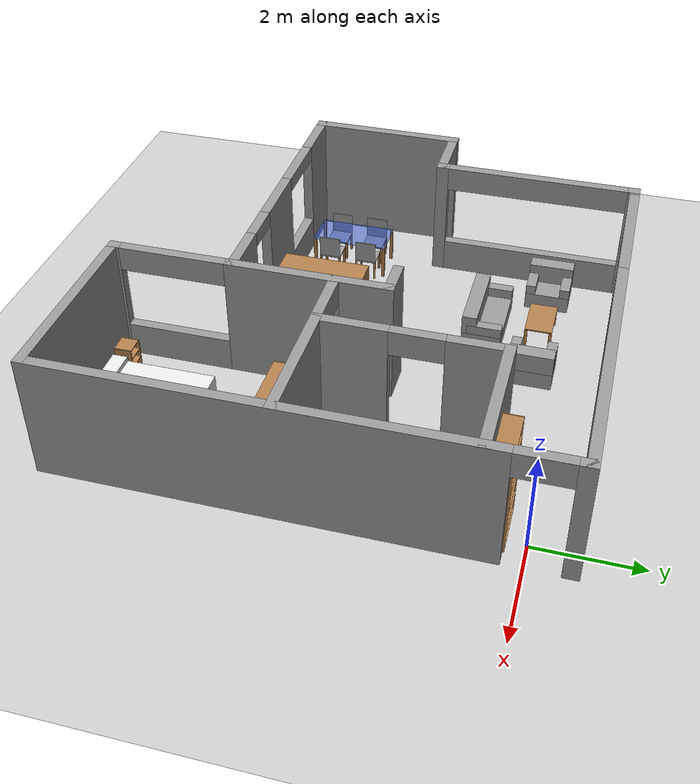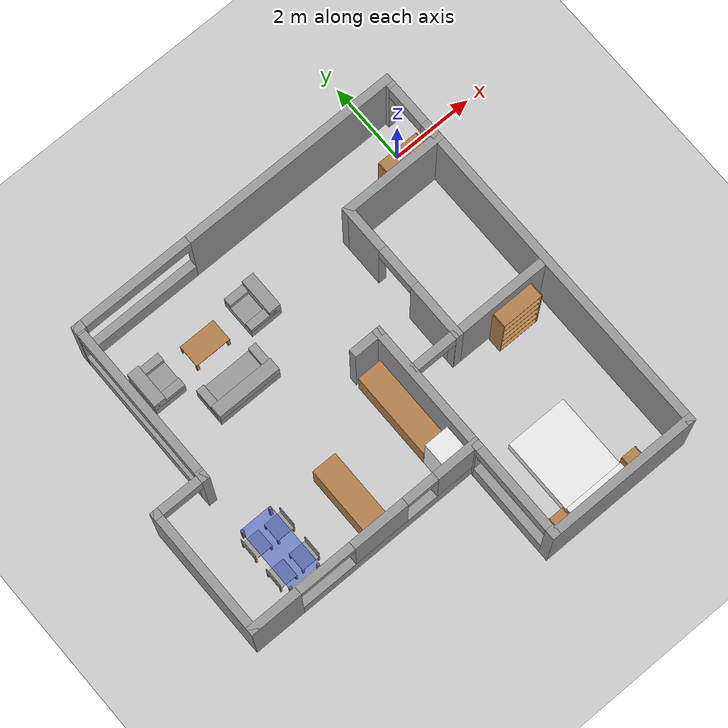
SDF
<sdf version="1.4">
 <world name="GrannyAnnie">
  <light name="sun" type="directional">
   <pose>0 0 10 0 -0 0</pose>
   <diffuse>0.8 0.8 0.8 1</diffuse>
   <specular>0.2 0.2 0.2 1</specular>
   <attenuation>
    <range>1000</range>
    <constant>0.9</constant>
    <linear>0.01</linear>
    <quadratic>0.001</quadratic>
   </attenuation>
   <direction>-0.5 0.1 -0.9</direction>
  </light>
  <model name="ground_plane">
   <static>1</static>
   <link name="link">
    <collision name="collision">
     <geometry><plane><normal>0 0 1</normal><size>100 100</size></plane></geometry>
     <surface><friction><ode><mu>100</mu><mu2>50</mu2></ode></friction></surface>
    </collision>
    <visual name="visual">
     <cast_shadows>0</cast_shadows>
     <geometry><plane><normal>0 0 1</normal><size>100 100</size></plane></geometry>
     <material>
      <script><uri>file://media/materials/scripts/gazebo.material</uri><name>Gazebo/Grey</name></script>
     </material>
    </visual>
    <velocity_decay><linear>0</linear><angular>0</angular></velocity_decay>
   </link>
  </model>
  <physics type="ode">
   <max_step_size>0.01</max_step_size>
   <real_time_factor>1</real_time_factor>
   <real_time_update_rate>100</real_time_update_rate>
   <gravity>0 0 -9.8</gravity>
  </physics>
  <scene><ambient>0.4 0.4 0.4 1</ambient><background>0.7 0.7 0.7 1</background><shadows>1</shadows></scene>
  <model name="mesa_comedor">
   <link name="mesa_link">
    <inertial>
     <pose>1.58603e-17 0 0.513571 0 -0 0</pose>
     <mass>7</mass>
     <inertia>
      <ixx>1.28229</ixx>
      <ixy>0</ixy>
      <ixz>5.70179e-17</ixz>
      <iyy>3.10629</iyy>
      <iyz>0</iyz>
      <izz>3.4192</izz>
     </inertia>
    </inertial>
    <collision name="mesa_link_collision">
     <pose>0 0 0.725 0 -0 0</pose>
     <geometry><box><size>1.6 0.8 0.03</size></box></geometry>
     <surface><friction><ode><mu>1</mu><mu2>1</mu2></ode></friction></surface>
    </collision>
    <collision name="mesa_link_collision_pata_1_link">
     <pose>0.77 0.37 0.355 0 -0 0</pose>
     <geometry><box><size>0.06 0.06 0.71</size></box></geometry>
     <surface><friction><ode><mu>1</mu><mu2>1</mu2></ode></friction></surface>
     <surface><friction><ode><mu>1</mu><mu2>1</mu2></ode></friction></surface>
    </collision>
    <collision name="mesa_link_collision_pata_2_link">
     <pose>0.77 -0.37 0.355 0 -0 0</pose>
     <geometry><box><size>0.06 0.06 0.71</size></box></geometry>
     <surface><friction><ode><mu>1</mu><mu2>1</mu2></ode></friction></surface>
     <surface><friction><ode><mu>1</mu><mu2>1</mu2></ode></friction></surface>
    </collision>
    <collision name="mesa_link_collision_pata_3_link">
     <pose>-0.77 -0.37 0.355 0 -0 0</pose>
     <geometry><box><size>0.06 0.06 0.71</size></box></geometry>
     <surface><friction><ode><mu>1</mu><mu2>1</mu2></ode></friction></surface>
     <surface><friction><ode><mu>1</mu><mu2>1</mu2></ode></friction></surface>
    </collision>
    <collision name="mesa_link_collision_pata_4_link">
     <pose>-0.77 0.37 0.355 0 -0 0</pose>
     <geometry><box><size>0.06 0.06 0.71</size></box></geometry>
     <surface><friction><ode><mu>1</mu><mu2>1</mu2></ode></friction></surface>
     <surface><friction><ode><mu>1</mu><mu2>1</mu2></ode></friction></surface>
    </collision>
    <visual name="mesa_link_visual">
     <pose>0 0 0.725 0 -0 0</pose>
     <geometry><box><size>1.6 0.8 0.03</size></box></geometry>
     <material><script><name>Gazebo/BlueTransparent</name><uri>__default__</uri></script></material>
    </visual>
    <visual name="mesa_link_visual_pata_1_link">
     <pose>0.77 0.37 0.355 0 -0 0</pose>
     <geometry><box><size>0.06 0.06 0.71</size></box></geometry>
     <material><script><name>Gazebo/Wood</name><uri>__default__</uri></script></material>
    </visual>
    <visual name="mesa_link_visual_pata_2_link">
     <pose>0.77 -0.37 0.355 0 -0 0</pose>
     <geometry><box><size>0.06 0.06 0.71</size></box></geometry>
     <material><script><name>Gazebo/Wood</name><uri>__default__</uri></script></material>
    </visual>
    <visual name="mesa_link_visual_pata_3_link">
     <pose>-0.77 -0.37 0.355 0 -0 0</pose>
     <geometry><box><size>0.06 0.06 0.71</size></box></geometry>
     <material><script><name>Gazebo/Wood</name><uri>__default__</uri></script></material>
    </visual>
    <visual name="mesa_link_visual_pata_4_link">
     <pose>-0.77 0.37 0.355 0 -0 0</pose>
     <geometry><box><size>0.06 0.06 0.71</size></box></geometry>
     <material><script><name>Gazebo/Wood</name><uri>__default__</uri></script></material>
    </visual>
    <velocity_decay><linear>0</linear><angular>0</angular></velocity_decay>
    <velocity_decay><linear>0</linear><angular>0</angular></velocity_decay>
    <velocity_decay><linear>0</linear><angular>0</angular></velocity_decay>
    <velocity_decay><linear>0</linear><angular>0</angular></velocity_decay>
    <velocity_decay><linear>0</linear><angular>0</angular></velocity_decay>
    <self_collide>1</self_collide>
   </link>
   <pose>-7.4 -5 0 0 -0 1.57</pose>
   <static>0</static>
  </model>
  <model name="RoCKIn@Home">
   <link name="Wall_12">
    <collision name="Wall_12_Collision">
     <geometry><box><size>2.6 0.2 2.5</size></box></geometry>
     <pose>0 0 1.25 0 -0 0</pose>
    </collision>
    <visual name="Wall_12_Visual">
     <pose>0 0 1.25 0 -0 0</pose>
     <geometry><box><size>2.6 0.2 2.5</size></box></geometry>
     <material>
      <script><uri>file://media/materials/scripts/gazebo.material</uri><name>Gazebo/Grey</name></script>
     </material>
    </visual>
    <velocity_decay><linear>0</linear><angular>0</angular></velocity_decay>
    <pose>7.8 1.205 0 0 -0 1.5708</pose>
   </link>
   <link name="Wall_14">
    <pose>6.0996 2.4048 0 0 -0 3.14159</pose>
    <visual name="Wall_14_Visual_0">
     <pose>-1.20789 0 1.25 0 -0 0</pose>
     <geometry><box><size>1.18422 0.2 2.5</size></box></geometry>
     <material>
      <script><uri>file://media/materials/scripts/gazebo.material</uri><name>Gazebo/Grey</name></script>
     </material>
    </visual>
    <collision name="Wall_14_Collision_0">
     <geometry><box><size>1.18422 0.2 2.5</size></box></geometry>
     <pose>-1.20789 0 1.25 0 -0 0</pose>
    </collision>
    <visual name="Wall_14_Visual_1">
     <pose>1.09211 0 1.25 0 -0 0</pose>
     <geometry><box><size>1.41579 0.2 2.5</size></box></geometry>
     <material>
      <script><uri>file://media/materials/scripts/gazebo.material</uri><name>Gazebo/Grey</name></script>
     </material>
    </visual>
    <collision name="Wall_14_Collision_1">
     <geometry><box><size>1.41579 0.2 2.5</size></box></geometry>
     <pose>1.09211 0 1.25 0 -0 0</pose>
    </collision>
    <visual name="Wall_14_Visual_2">
     <pose>-0.115785 0 2.25 0 -0 0</pose>
     <geometry><box><size>1 0.2 0.5</size></box></geometry>
     <material>
      <script><uri>file://media/materials/scripts/gazebo.material</uri><name>Gazebo/Grey</name></script>
     </material>
    </visual>
    <collision name="Wall_14_Collision_2">
     <geometry><box><size>1 0.2 0.5</size></box></geometry>
     <pose>-0.115785 0 2.25 0 -0 0</pose>
    </collision>
    <velocity_decay><linear>0</linear><angular>0</angular></velocity_decay>
   </link>
   <link name="Wall_16">
    <collision name="Wall_16_Collision">
     <geometry><box><size>2.60492 0.2 2.5</size></box></geometry>
     <pose>0 0 1.25 0 -0 0</pose>
    </collision>
    <visual name="Wall_16_Visual">
     <pose>0 0 1.25 0 -0 0</pose>
     <geometry><box><size>2.60492 0.2 2.5</size></box></geometry>
     <material>
      <script><uri>file://media/materials/scripts/gazebo.material</uri><name>Gazebo/Grey</name></script>
     </material>
    </visual>
    <velocity_decay><linear>0</linear><angular>0</angular></velocity_decay>
    <pose>4.39903 1.20277 0 0 -0 1.5708</pose>
   </link>
   <link name="Wall_18">
    <collision name="Wall_18_Collision">
     <geometry><box><size>3.8 0.2 2.5</size></box></geometry>
     <pose>0 0 1.25 0 -0 0</pose>
    </collision>
    <visual name="Wall_18_Visual">
     <pose>0 0 1.25 0 -0 0</pose>
     <geometry><box><size>3.8 0.2 2.5</size></box></geometry>
     <material>
      <script><uri>file://media/materials/scripts/gazebo.material</uri><name>Gazebo/Grey</name></script>
     </material>
    </visual>
    <velocity_decay><linear>0</linear><angular>0</angular></velocity_decay>
    <pose>0.024876 1.80003 0 0 -0 1.5708</pose>
   </link>
   <link name="Wall_2">
    <pose>4.7266 0 0 0 -0 0</pose>
    <visual name="Wall_2_Visual_0">
     <pose>-0.649274 0 1.25 0 -0 0</pose>
     <geometry><box><size>8.30145 0.2 2.5</size></box></geometry>
     <material>
      <script><uri>file://media/materials/scripts/gazebo.material</uri><name>Gazebo/Grey</name></script>
     </material>
    </visual>
    <collision name="Wall_2_Collision_0">
     <geometry><box><size>8.30145 0.2 2.5</size></box></geometry>
     <pose>-0.649274 0 1.25 0 -0 0</pose>
    </collision>
    <visual name="Wall_2_Visual_1">
     <pose>4.65073 0 1.25 0 -0 0</pose>
     <geometry><box><size>0.298547 0.2 2.5</size></box></geometry>
     <material>
      <script><uri>file://media/materials/scripts/gazebo.material</uri><name>Gazebo/Grey</name></script>
     </material>
    </visual>
    <collision name="Wall_2_Collision_1">
     <geometry><box><size>0.298547 0.2 2.5</size></box></geometry>
     <pose>4.65073 0 1.25 0 -0 0</pose>
    </collision>
    <visual name="Wall_2_Visual_2">
     <pose>4.00145 0 2.25 0 -0 0</pose>
     <geometry><box><size>1 0.2 0.5</size></box></geometry>
     <material>
      <script><uri>file://media/materials/scripts/gazebo.material</uri><name>Gazebo/Grey</name></script>
     </material>
    </visual>
    <collision name="Wall_2_Collision_2">
     <geometry><box><size>1 0.2 0.5</size></box></geometry>
     <pose>4.00145 0 2.25 0 -0 0</pose>
    </collision>
    <velocity_decay><linear>0</linear><angular>0</angular></velocity_decay>
   </link>
   <link name="Wall_20">
    <pose>2.72456 3.60059 0 0 -0 0</pose>
    <visual name="Wall_20_Visual_0">
     <pose>-2.67396 0 1.25 0 -0 0</pose>
     <geometry><box><size>0.251208 0.2 2.5</size></box></geometry>
     <material>
      <script><uri>file://media/materials/scripts/gazebo.material</uri><name>Gazebo/Grey</name></script>
     </material>
    </visual>
    <collision name="Wall_20_Collision_0">
     <geometry><box><size>0.251208 0.2 2.5</size></box></geometry>
     <pose>-2.67396 0 1.25 0 -0 0</pose>
    </collision>
    <visual name="Wall_20_Visual_1">
     <pose>1.1766 0 1.25 0 -0 0</pose>
     <geometry><box><size>3.24591 0.2 2.5</size></box></geometry>
     <material>
      <script><uri>file://media/materials/scripts/gazebo.material</uri><name>Gazebo/Grey</name></script>
     </material>
    </visual>
    <collision name="Wall_20_Collision_1">
     <geometry><box><size>3.24591 0.2 2.5</size></box></geometry>
     <pose>1.1766 0 1.25 0 -0 0</pose>
    </collision>
    <visual name="Wall_20_Visual_2">
     <pose>-1.49735 0 2.25 0 -0 0</pose>
     <geometry><box><size>2.102 0.2 0.5</size></box></geometry>
     <material>
      <script><uri>file://media/materials/scripts/gazebo.material</uri><name>Gazebo/Grey</name></script>
     </material>
    </visual>
    <collision name="Wall_20_Collision_2">
     <geometry><box><size>2.102 0.2 0.5</size></box></geometry>
     <pose>-1.49735 0 2.25 0 -0 0</pose>
    </collision>
    <visual name="Wall_20_Visual_3">
     <pose>-1.49735 0 0.35 0 -0 0</pose>
     <geometry><box><size>2.102 0.2 0.7</size></box></geometry>
     <material>
      <script><uri>file://media/materials/scripts/gazebo.material</uri><name>Gazebo/Grey</name></script>
     </material>
    </visual>
    <collision name="Wall_20_Collision_3">
     <geometry><box><size>2.102 0.2 0.3</size></box></geometry>
     <pose>-1.49735 0 0.35 0 -0 0</pose>
    </collision>
    <velocity_decay><linear>0</linear><angular>0</angular></velocity_decay>
   </link>
   <link name="Wall_22">
    <pose>4.39856 3.00206 0 0 -0 1.5708</pose>
    <visual name="Wall_22_Visual_0">
     <pose>-0.601085 0 1.25 0 -0 0</pose>
     <geometry><box><size>0.194709 0.2 2.5</size></box></geometry>
     <material>
      <script><uri>file://media/materials/scripts/gazebo.material</uri><name>Gazebo/Grey</name></script>
     </material>
    </visual>
    <collision name="Wall_22_Collision_0">
     <geometry><box><size>0.194709 0.2 2.5</size></box></geometry>
     <pose>-0.601085 0 1.25 0 -0 0</pose>
    </collision>
    <visual name="Wall_22_Visual_1">
     <pose>0.597355 0 1.25 0 -0 0</pose>
     <geometry><box><size>0.202171 0.2 2.5</size></box></geometry>
     <material>
      <script><uri>file://media/materials/scripts/gazebo.material</uri><name>Gazebo/Grey</name></script>
     </material>
    </visual>
    <collision name="Wall_22_Collision_1">
     <geometry><box><size>0.202171 0.2 2.5</size></box></geometry>
     <pose>0.597355 0 1.25 0 -0 0</pose>
    </collision>
    <visual name="Wall_22_Visual_2">
     <pose>-0.003731 0 2.25 0 -0 0</pose>
     <geometry><box><size>1 0.2 0.5</size></box></geometry>
     <material>
      <script><uri>file://media/materials/scripts/gazebo.material</uri><name>Gazebo/Grey</name></script>
     </material>
    </visual>
    <collision name="Wall_22_Collision_2">
     <geometry><box><size>1 0.2 0.5</size></box></geometry>
     <pose>-0.003731 0 2.25 0 -0 0</pose>
    </collision>
    <velocity_decay><linear>0</linear><angular>0</angular></velocity_decay>
   </link>
   <link name="Wall_24">
    <pose>7.42703 8.20242 0 0 -0 3.14159</pose>
    <visual name="Wall_24_Visual_0">
     <pose>-1.97924 0 1.25 0 -0 0</pose>
     <geometry><box><size>0.241529 0.2 2.5</size></box></geometry>
     <material>
      <script><uri>file://media/materials/scripts/gazebo.material</uri><name>Gazebo/Grey</name></script>
     </material>
    </visual>
    <collision name="Wall_24_Collision_0">
     <geometry><box><size>0.241529 0.2 2.5</size></box></geometry>
     <pose>-1.97924 0 1.25 0 -0 0</pose>
    </collision>
    <visual name="Wall_24_Visual_1">
     <pose>1.97395 0 1.25 0 -0 0</pose>
     <geometry><box><size>0.252091 0.2 2.5</size></box></geometry>
     <material>
      <script><uri>file://media/materials/scripts/gazebo.material</uri><name>Gazebo/Grey</name></script>
     </material>
    </visual>
    <collision name="Wall_24_Collision_1">
     <geometry><box><size>0.252091 0.2 2.5</size></box></geometry>
     <pose>1.97395 0 1.25 0 -0 0</pose>
    </collision>
    <visual name="Wall_24_Visual_2">
     <pose>-0.005281 0 2.25 0 -0 0</pose>
     <geometry><box><size>3.70638 0.2 0.5</size></box></geometry>
     <material>
      <script><uri>file://media/materials/scripts/gazebo.material</uri><name>Gazebo/Grey</name></script>
     </material>
    </visual>
    <collision name="Wall_24_Collision_2">
     <geometry><box><size>3.70638 0.2 0.5</size></box></geometry>
     <pose>-0.005281 0 2.25 0 -0 0</pose>
    </collision>
    <visual name="Wall_24_Visual_3">
     <pose>-0.005281 0 0.35 0 -0 0</pose>
     <geometry><box><size>3.70638 0.2 0.7</size></box></geometry>
     <material>
      <script><uri>file://media/materials/scripts/gazebo.material</uri><name>Gazebo/Grey</name></script>
     </material>
    </visual>
    <collision name="Wall_24_Collision_3">
     <geometry><box><size>3.70638 0.2 0.7</size></box></geometry>
     <pose>-0.005281 0 0.35 0 -0 0</pose>
    </collision>
    <velocity_decay><linear>0</linear><angular>0</angular></velocity_decay>
   </link>
   <link name="Wall_28">
    <collision name="Wall_28_Collision">
     <geometry><box><size>3.2 0.2 2.5</size></box></geometry>
     <pose>0 0 1.25 0 -0 0</pose>
    </collision>
    <visual name="Wall_28_Visual">
     <pose>0 0 1.25 0 -0 0</pose>
     <geometry><box><size>3.2 0.2 2.5</size></box></geometry>
     <material>
      <script><uri>file://media/materials/scripts/gazebo.material</uri><name>Gazebo/Grey</name></script>
     </material>
    </visual>
    <velocity_decay><linear>0</linear><angular>0</angular></velocity_decay>
    <pose>3.92571 9.40229 0 0 -0 3.14159</pose>
   </link>
   <link name="Wall_30">
    <pose>2.42541 6.50159 0 0 0 -1.5708</pose>
    <visual name="Wall_30_Visual_0">
     <pose>-2.363 0 1.25 0 -0 0</pose>
     <geometry><box><size>1.27269 0.2 2.5</size></box></geometry>
     <material>
      <script><uri>file://media/materials/scripts/gazebo.material</uri><name>Gazebo/Grey</name></script>
     </material>
    </visual>
    <collision name="Wall_30_Collision_0">
     <geometry><box><size>1.27269 0.2 2.5</size></box></geometry>
     <pose>-2.363 0 1.25 0 -0 0</pose>
    </collision>
    <visual name="Wall_30_Visual_1">
     <pose>0.636346 0 0.35 0 -0 0</pose>
     <geometry><box><size>4.726 0.2 0.7</size></box></geometry>
     <material>
      <script><uri>file://media/materials/scripts/gazebo.material</uri><name>Gazebo/Grey</name></script>
     </material>
    </visual>
    <collision name="Wall_30_Collision_1">
     <geometry><box><size>4.726 0.2 0.7</size></box></geometry>
     <pose>0.636346 0 0.35 0 -0 0</pose>
    </collision>
    <visual name="Wall_30_Visual_2">
     <pose>0.36359 0 1.6 0 -0 0</pose>
     <geometry><box><size>1.38049 0.2 1.8</size></box></geometry>
     <material>
      <script><uri>file://media/materials/scripts/gazebo.material</uri><name>Gazebo/Grey</name></script>
     </material>
    </visual>
    <collision name="Wall_30_Collision_2">
     <geometry><box><size>1.38049 0.2 1.8</size></box></geometry>
     <pose>0.36359 0 1.6 0 -0 0</pose>
    </collision>
    <visual name="Wall_30_Visual_3">
     <pose>2.42659 0 1.6 0 -0 0</pose>
     <geometry><box><size>1.14551 0.2 1.8</size></box></geometry>
     <material>
      <script><uri>file://media/materials/scripts/gazebo.material</uri><name>Gazebo/Grey</name></script>
     </material>
    </visual>
    <collision name="Wall_30_Collision_3">
     <geometry><box><size>1.14551 0.2 1.8</size></box></geometry>
     <pose>2.42659 0 1.6 0 -0 0</pose>
    </collision>
    <visual name="Wall_30_Visual_4">
     <pose>-1.02665 0 2.35 0 -0 0</pose>
     <geometry><box><size>1.4 0.2 0.3</size></box></geometry>
     <material>
      <script><uri>file://media/materials/scripts/gazebo.material</uri><name>Gazebo/Grey</name></script>
     </material>
    </visual>
    <collision name="Wall_30_Collision_4">
     <geometry><box><size>1.4 0.2 0.3</size></box></geometry>
     <pose>-1.02665 0 2.35 0 -0 0</pose>
    </collision>
    <visual name="Wall_30_Visual_5">
     <pose>1.45383 0 2.35 0 -0 0</pose>
     <geometry><box><size>0.8 0.2 0.3</size></box></geometry>
     <material>
      <script><uri>file://media/materials/scripts/gazebo.material</uri><name>Gazebo/Grey</name></script>
     </material>
    </visual>
    <collision name="Wall_30_Collision_5">
     <geometry><box><size>0.8 0.2 0.3</size></box></geometry>
     <pose>1.45383 0 2.35 0 -0 0</pose>
    </collision>
    <velocity_decay><linear>0</linear><angular>0</angular></velocity_decay>
   </link>
   <link name="Wall_32">
    <pose>5.42654 8.80216 0 0 0 -1.5708</pose>
    <visual name="Wall_32_Visual_0">
     <pose>-0.599775 0 1.25 0 -0 0</pose>
     <geometry><box><size>0.199231 0.2 2.5</size></box></geometry>
     <material>
      <script><uri>file://media/materials/scripts/gazebo.material</uri><name>Gazebo/Grey</name></script>
     </material>
    </visual>
    <collision name="Wall_32_Collision_0">
     <geometry><box><size>0.199231 0.2 2.5</size></box></geometry>
     <pose>-0.599775 0 1.25 0 -0 0</pose>
    </collision>
    <visual name="Wall_32_Visual_1">
     <pose>0.599615 0 1.25 0 -0 0</pose>
     <geometry><box><size>0.199549 0.2 2.5</size></box></geometry>
     <material>
      <script><uri>file://media/materials/scripts/gazebo.material</uri><name>Gazebo/Grey</name></script>
     </material>
    </visual>
    <collision name="Wall_32_Collision_1">
     <geometry><box><size>0.199549 0.2 2.5</size></box></geometry>
     <pose>0.599615 0 1.25 0 -0 0</pose>
    </collision>
    <visual name="Wall_32_Visual_2">
     <pose>-0.000159 0 2.25 0 -0 0</pose>
     <geometry><box><size>1 0.2 0.5</size></box></geometry>
     <material>
      <script><uri>file://media/materials/scripts/gazebo.material</uri><name>Gazebo/Grey</name></script>
     </material>
    </visual>
    <collision name="Wall_32_Collision_2">
     <geometry><box><size>1 0.2 0.5</size></box></geometry>
     <pose>-0.000159 0 2.25 0 -0 0</pose>
    </collision>
    <velocity_decay><linear>0</linear><angular>0</angular></velocity_decay>
   </link>
   <link name="Wall_35">
    <collision name="Wall_35_Collision">
     <geometry><box><size>0.8 0.2 2.5</size></box></geometry>
     <pose>0 0 1.25 0 -0 0</pose>
    </collision>
    <visual name="Wall_35_Visual">
     <pose>0 0 1.25 0 -0 0</pose>
     <geometry><box><size>0.8 0.2 2.5</size></box></geometry>
     <material>
      <script><uri>file://media/materials/scripts/gazebo.material</uri><name>Gazebo/Grey</name></script>
     </material>
    </visual>
    <velocity_decay><linear>0</linear><angular>0</angular></velocity_decay>
    <pose>5.42451 3.90082 0 0 -0 1.5708</pose>
   </link>
   <link name="Wall_8">
    <pose>9.42875 4.1026 0 0 -0 1.5708</pose>
    <visual name="Wall_8_Visual_0">
     <pose>-1.48935 0 1.25 0 -0 0</pose>
     <geometry><box><size>5.42201 0.2 2.5</size></box></geometry>
     <material>
      <script><uri>file://media/materials/scripts/gazebo.material</uri><name>Gazebo/Grey</name></script>
     </material>
    </visual>
    <collision name="Wall_8_Collision_0">
     <geometry><box><size>5.42201 0.2 2.5</size></box></geometry>
     <pose>-1.48935 0 1.25 0 -0 0</pose>
    </collision>
    <visual name="Wall_8_Visual_1">
     <pose>4.07465 0 1.25 0 -0 0</pose>
     <geometry><box><size>0.251416 0.2 2.5</size></box></geometry>
     <material>
      <script><uri>file://media/materials/scripts/gazebo.material</uri><name>Gazebo/Grey</name></script>
     </material>
    </visual>
    <collision name="Wall_8_Collision_1">
     <geometry><box><size>0.251416 0.2 2.5</size></box></geometry>
     <pose>4.07465 0 1.25 0 -0 0</pose>
    </collision>
    <visual name="Wall_8_Visual_2">
     <pose>2.5853 0 2.25 0 -0 0</pose>
     <geometry><box><size>2.72728 0.2 0.5</size></box></geometry>
     <material>
      <script><uri>file://media/materials/scripts/gazebo.material</uri><name>Gazebo/Grey</name></script>
     </material>
    </visual>
    <collision name="Wall_8_Collision_2">
     <geometry><box><size>2.72728 0.2 0.5</size></box></geometry>
     <pose>2.5853 0 2.25 0 -0 0</pose>
    </collision>
    <visual name="Wall_8_Visual_3">
     <pose>2.5853 0 0.35 0 -0 0</pose>
     <geometry><box><size>2.72728 0.2 0.7</size></box></geometry>
     <material>
      <script><uri>file://media/materials/scripts/gazebo.material</uri><name>Gazebo/Grey</name></script>
     </material>
    </visual>
    <collision name="Wall_8_Collision_3">
     <geometry><box><size>2.72728 0.2 0.7</size></box></geometry>
     <pose>2.5853 0 0.35 0 -0 0</pose>
    </collision>
    <velocity_decay><linear>0</linear><angular>0</angular></velocity_decay>
   </link>
   <static>1</static>
   <pose>0.4 -8.6 0 0 -0 1.57</pose>
  </model>
  <model name="silla_1">
   <link name="silla_link">
    <inertial>
     <pose>0.0215 0 0.353 0 -0 0</pose>
     <mass>2</mass>
     <inertia>
      <ixx>0.674432</ixx>
      <ixy>0</ixy>
      <ixz>-0.012986</ixz>
      <iyy>0.682753</iyy>
      <iyz>0</iyz>
      <izz>0.675561</izz>
     </inertia>
    </inertial>
    <collision name="silla_link_collision">
     <pose>0 0 0.415 0 -0 0</pose>
     <geometry><box><size>0.45 0.45 0.03</size></box></geometry>
     <surface><friction><ode><mu>1</mu><mu2>1</mu2></ode></friction></surface>
    </collision>
    <collision name="silla_link_collision_pata_1_link">
     <pose>0.205 0.205 0.2 0 -0 0</pose>
     <geometry><box><size>0.04 0.04 0.4</size></box></geometry>
     <surface><friction><ode><mu>1</mu><mu2>1</mu2></ode></friction></surface>
     <surface><friction><ode><mu>1</mu><mu2>1</mu2></ode></friction></surface>
    </collision>
    <collision name="silla_link_collision_pata_2_link">
     <pose>0.205 -0.205 0.2 0 -0 0</pose>
     <geometry><box><size>0.04 0.04 0.4</size></box></geometry>
     <surface><friction><ode><mu>1</mu><mu2>1</mu2></ode></friction></surface>
     <surface><friction><ode><mu>1</mu><mu2>1</mu2></ode></friction></surface>
    </collision>
    <collision name="silla_link_collision_pata_3_link">
     <pose>-0.205 -0.205 0.2 0 -0 0</pose>
     <geometry><box><size>0.04 0.04 0.4</size></box></geometry>
     <surface><friction><ode><mu>1</mu><mu2>1</mu2></ode></friction></surface>
     <surface><friction><ode><mu>1</mu><mu2>1</mu2></ode></friction></surface>
    </collision>
    <collision name="silla_link_collision_pata_4_link">
     <pose>-0.205 0.205 0.2 0 -0 0</pose>
     <geometry><box><size>0.04 0.04 0.4</size></box></geometry>
     <surface><friction><ode><mu>1</mu><mu2>1</mu2></ode></friction></surface>
     <surface><friction><ode><mu>1</mu><mu2>1</mu2></ode></friction></surface>
    </collision>
    <collision name="silla_link_collision_respaldo_link">
     <pose>0.215 0 0.655 0 -0 0</pose>
     <geometry><box><size>0.02 0.45 0.45</size></box></geometry>
     <surface><friction><ode><mu>1</mu><mu2>1</mu2></ode></friction></surface>
     <surface><friction><ode><mu>1</mu><mu2>1</mu2></ode></friction></surface>
    </collision>
    <visual name="silla_link_visual">
     <pose>0 0 0.415 0 -0 0</pose>
     <geometry><box><size>0.45 0.45 0.03</size></box></geometry>
     <material><script><name>Gazebo/Grey</name><uri>__default__</uri></script></material>
    </visual>
    <visual name="silla_link_visual_pata_1_link">
     <pose>0.205 0.205 0.2 0 -0 0</pose>
     <geometry><box><size>0.04 0.04 0.4</size></box></geometry>
     <material><script><name>Gazebo/Wood</name><uri>__default__</uri></script></material>
    </visual>
    <visual name="silla_link_visual_pata_2_link">
     <pose>0.205 -0.205 0.2 0 -0 0</pose>
     <geometry><box><size>0.04 0.04 0.4</size></box></geometry>
     <material><script><name>Gazebo/Wood</name><uri>__default__</uri></script></material>
    </visual>
    <visual name="silla_link_visual_pata_3_link">
     <pose>-0.205 -0.205 0.2 0 -0 0</pose>
     <geometry><box><size>0.04 0.04 0.4</size></box></geometry>
     <material><script><name>Gazebo/Wood</name><uri>__default__</uri></script></material>
    </visual>
    <visual name="silla_link_visual_pata_4_link">
     <pose>-0.205 0.205 0.2 0 -0 0</pose>
     <geometry><box><size>0.04 0.04 0.4</size></box></geometry>
     <material><script><name>Gazebo/Wood</name><uri>__default__</uri></script></material>
    </visual>
    <visual name="silla_link_visual_respaldo_link">
     <pose>0.215 0 0.655 0 -0 0</pose>
     <geometry><box><size>0.02 0.45 0.45</size></box></geometry>
     <material><script><name>Gazebo/Grey</name><uri>__default__</uri></script></material>
    </visual>
    <velocity_decay><linear>0</linear><angular>0</angular></velocity_decay>
    <velocity_decay><linear>0</linear><angular>0</angular></velocity_decay>
    <velocity_decay><linear>0</linear><angular>0</angular></velocity_decay>
    <velocity_decay><linear>0</linear><angular>0</angular></velocity_decay>
    <velocity_decay><linear>0</linear><angular>0</angular></velocity_decay>
    <velocity_decay><linear>0</linear><angular>0</angular></velocity_decay>
    <self_collide>1</self_collide>
   </link>
   <pose>-7.1 -5.4 0 0 -0 0</pose>
   <static>0</static>
  </model>
  <model name="silla_2">
   <link name="silla_link">
    <inertial>
     <pose>0.0215 0 0.353 0 -0 0</pose>
     <mass>2</mass>
     <inertia>
      <ixx>0.674432</ixx>
      <ixy>0</ixy>
      <ixz>-0.012986</ixz>
      <iyy>0.682753</iyy>
      <iyz>0</iyz>
      <izz>0.675561</izz>
     </inertia>
    </inertial>
    <collision name="silla_link_collision">
     <pose>0 0 0.415 0 -0 0</pose>
     <geometry><box><size>0.45 0.45 0.03</size></box></geometry>
     <surface><friction><ode><mu>1</mu><mu2>1</mu2></ode></friction></surface>
    </collision>
    <collision name="silla_link_collision_pata_1_link">
     <pose>0.205 0.205 0.2 0 -0 0</pose>
     <geometry><box><size>0.04 0.04 0.4</size></box></geometry>
     <surface><friction><ode><mu>1</mu><mu2>1</mu2></ode></friction></surface>
     <surface><friction><ode><mu>1</mu><mu2>1</mu2></ode></friction></surface>
    </collision>
    <collision name="silla_link_collision_pata_2_link">
     <pose>0.205 -0.205 0.2 0 -0 0</pose>
     <geometry><box><size>0.04 0.04 0.4</size></box></geometry>
     <surface><friction><ode><mu>1</mu><mu2>1</mu2></ode></friction></surface>
     <surface><friction><ode><mu>1</mu><mu2>1</mu2></ode></friction></surface>
    </collision>
    <collision name="silla_link_collision_pata_3_link">
     <pose>-0.205 -0.205 0.2 0 -0 0</pose>
     <geometry><box><size>0.04 0.04 0.4</size></box></geometry>
     <surface><friction><ode><mu>1</mu><mu2>1</mu2></ode></friction></surface>
     <surface><friction><ode><mu>1</mu><mu2>1</mu2></ode></friction></surface>
    </collision>
    <collision name="silla_link_collision_pata_4_link">
     <pose>-0.205 0.205 0.2 0 -0 0</pose>
     <geometry><box><size>0.04 0.04 0.4</size></box></geometry>
     <surface><friction><ode><mu>1</mu><mu2>1</mu2></ode></friction></surface>
     <surface><friction><ode><mu>1</mu><mu2>1</mu2></ode></friction></surface>
    </collision>
    <collision name="silla_link_collision_respaldo_link">
     <pose>0.215 0 0.655 0 -0 0</pose>
     <geometry><box><size>0.02 0.45 0.45</size></box></geometry>
     <surface><friction><ode><mu>1</mu><mu2>1</mu2></ode></friction></surface>
     <surface><friction><ode><mu>1</mu><mu2>1</mu2></ode></friction></surface>
    </collision>
    <visual name="silla_link_visual">
     <pose>0 0 0.415 0 -0 0</pose>
     <geometry><box><size>0.45 0.45 0.03</size></box></geometry>
     <material><script><name>Gazebo/Grey</name><uri>__default__</uri></script></material>
    </visual>
    <visual name="silla_link_visual_pata_1_link">
     <pose>0.205 0.205 0.2 0 -0 0</pose>
     <geometry><box><size>0.04 0.04 0.4</size></box></geometry>
     <material><script><name>Gazebo/Wood</name><uri>__default__</uri></script></material>
    </visual>
    <visual name="silla_link_visual_pata_2_link">
     <pose>0.205 -0.205 0.2 0 -0 0</pose>
     <geometry><box><size>0.04 0.04 0.4</size></box></geometry>
     <material><script><name>Gazebo/Wood</name><uri>__default__</uri></script></material>
    </visual>
    <visual name="silla_link_visual_pata_3_link">
     <pose>-0.205 -0.205 0.2 0 -0 0</pose>
     <geometry><box><size>0.04 0.04 0.4</size></box></geometry>
     <material><script><name>Gazebo/Wood</name><uri>__default__</uri></script></material>
    </visual>
    <visual name="silla_link_visual_pata_4_link">
     <pose>-0.205 0.205 0.2 0 -0 0</pose>
     <geometry><box><size>0.04 0.04 0.4</size></box></geometry>
     <material><script><name>Gazebo/Wood</name><uri>__default__</uri></script></material>
    </visual>
    <visual name="silla_link_visual_respaldo_link">
     <pose>0.215 0 0.655 0 -0 0</pose>
     <geometry><box><size>0.02 0.45 0.45</size></box></geometry>
     <material><script><name>Gazebo/Grey</name><uri>__default__</uri></script></material>
    </visual>
    <velocity_decay><linear>0</linear><angular>0</angular></velocity_decay>
    <velocity_decay><linear>0</linear><angular>0</angular></velocity_decay>
    <velocity_decay><linear>0</linear><angular>0</angular></velocity_decay>
    <velocity_decay><linear>0</linear><angular>0</angular></velocity_decay>
    <velocity_decay><linear>0</linear><angular>0</angular></velocity_decay>
    <velocity_decay><linear>0</linear><angular>0</angular></velocity_decay>
    <self_collide>1</self_collide>
   </link>
   <pose>-7.1 -4.6 0 0 -0 0</pose>
   <static>0</static>
  </model>
  <model name="silla_3">
   <link name="silla_link">
    <inertial>
     <pose>0.0215 0 0.353 0 -0 0</pose>
     <mass>2</mass>
     <inertia>
      <ixx>0.674432</ixx>
      <ixy>0</ixy>
      <ixz>-0.012986</ixz>
      <iyy>0.682753</iyy>
      <iyz>0</iyz>
      <izz>0.675561</izz>
     </inertia>
    </inertial>
    <collision name="silla_link_collision">
     <pose>0 0 0.415 0 -0 0</pose>
     <geometry><box><size>0.45 0.45 0.03</size></box></geometry>
     <surface><friction><ode><mu>1</mu><mu2>1</mu2></ode></friction></surface>
    </collision>
    <collision name="silla_link_collision_pata_1_link">
     <pose>0.205 0.205 0.2 0 -0 0</pose>
     <geometry><box><size>0.04 0.04 0.4</size></box></geometry>
     <surface><friction><ode><mu>1</mu><mu2>1</mu2></ode></friction></surface>
     <surface><friction><ode><mu>1</mu><mu2>1</mu2></ode></friction></surface>
    </collision>
    <collision name="silla_link_collision_pata_2_link">
     <pose>0.205 -0.205 0.2 0 -0 0</pose>
     <geometry><box><size>0.04 0.04 0.4</size></box></geometry>
     <surface><friction><ode><mu>1</mu><mu2>1</mu2></ode></friction></surface>
     <surface><friction><ode><mu>1</mu><mu2>1</mu2></ode></friction></surface>
    </collision>
    <collision name="silla_link_collision_pata_3_link">
     <pose>-0.205 -0.205 0.2 0 -0 0</pose>
     <geometry><box><size>0.04 0.04 0.4</size></box></geometry>
     <surface><friction><ode><mu>1</mu><mu2>1</mu2></ode></friction></surface>
     <surface><friction><ode><mu>1</mu><mu2>1</mu2></ode></friction></surface>
    </collision>
    <collision name="silla_link_collision_pata_4_link">
     <pose>-0.205 0.205 0.2 0 -0 0</pose>
     <geometry><box><size>0.04 0.04 0.4</size></box></geometry>
     <surface><friction><ode><mu>1</mu><mu2>1</mu2></ode></friction></surface>
     <surface><friction><ode><mu>1</mu><mu2>1</mu2></ode></friction></surface>
    </collision>
    <collision name="silla_link_collision_respaldo_link">
     <pose>0.215 0 0.655 0 -0 0</pose>
     <geometry><box><size>0.02 0.45 0.45</size></box></geometry>
     <surface><friction><ode><mu>1</mu><mu2>1</mu2></ode></friction></surface>
     <surface><friction><ode><mu>1</mu><mu2>1</mu2></ode></friction></surface>
    </collision>
    <visual name="silla_link_visual">
     <pose>0 0 0.415 0 -0 0</pose>
     <geometry><box><size>0.45 0.45 0.03</size></box></geometry>
     <material><script><name>Gazebo/Grey</name><uri>__default__</uri></script></material>
    </visual>
    <visual name="silla_link_visual_pata_1_link">
     <pose>0.205 0.205 0.2 0 -0 0</pose>
     <geometry><box><size>0.04 0.04 0.4</size></box></geometry>
     <material><script><name>Gazebo/Wood</name><uri>__default__</uri></script></material>
    </visual>
    <visual name="silla_link_visual_pata_2_link">
     <pose>0.205 -0.205 0.2 0 -0 0</pose>
     <geometry><box><size>0.04 0.04 0.4</size></box></geometry>
     <material><script><name>Gazebo/Wood</name><uri>__default__</uri></script></material>
    </visual>
    <visual name="silla_link_visual_pata_3_link">
     <pose>-0.205 -0.205 0.2 0 -0 0</pose>
     <geometry><box><size>0.04 0.04 0.4</size></box></geometry>
     <material><script><name>Gazebo/Wood</name><uri>__default__</uri></script></material>
    </visual>
    <visual name="silla_link_visual_pata_4_link">
     <pose>-0.205 0.205 0.2 0 -0 0</pose>
     <geometry><box><size>0.04 0.04 0.4</size></box></geometry>
     <material><script><name>Gazebo/Wood</name><uri>__default__</uri></script></material>
    </visual>
    <visual name="silla_link_visual_respaldo_link">
     <pose>0.215 0 0.655 0 -0 0</pose>
     <geometry><box><size>0.02 0.45 0.45</size></box></geometry>
     <material><script><name>Gazebo/Grey</name><uri>__default__</uri></script></material>
    </visual>
    <velocity_decay><linear>0</linear><angular>0</angular></velocity_decay>
    <velocity_decay><linear>0</linear><angular>0</angular></velocity_decay>
    <velocity_decay><linear>0</linear><angular>0</angular></velocity_decay>
    <velocity_decay><linear>0</linear><angular>0</angular></velocity_decay>
    <velocity_decay><linear>0</linear><angular>0</angular></velocity_decay>
    <velocity_decay><linear>0</linear><angular>0</angular></velocity_decay>
    <self_collide>1</self_collide>
   </link>
   <pose>-7.7 -5.4 0 0 -0 3.14</pose>
   <static>0</static>
  </model>
  <model name="silla_4">
   <link name="silla_link">
    <inertial>
     <pose>0.0215 0 0.353 0 -0 0</pose>
     <mass>2</mass>
     <inertia>
      <ixx>0.674432</ixx>
      <ixy>0</ixy>
      <ixz>-0.012986</ixz>
      <iyy>0.682753</iyy>
      <iyz>0</iyz>
      <izz>0.675561</izz>
     </inertia>
    </inertial>
    <collision name="silla_link_collision">
     <pose>0 0 0.415 0 -0 0</pose>
     <geometry><box><size>0.45 0.45 0.03</size></box></geometry>
     <surface><friction><ode><mu>1</mu><mu2>1</mu2></ode></friction></surface>
    </collision>
    <collision name="silla_link_collision_pata_1_link">
     <pose>0.205 0.205 0.2 0 -0 0</pose>
     <geometry><box><size>0.04 0.04 0.4</size></box></geometry>
     <surface><friction><ode><mu>1</mu><mu2>1</mu2></ode></friction></surface>
     <surface><friction><ode><mu>1</mu><mu2>1</mu2></ode></friction></surface>
    </collision>
    <collision name="silla_link_collision_pata_2_link">
     <pose>0.205 -0.205 0.2 0 -0 0</pose>
     <geometry><box><size>0.04 0.04 0.4</size></box></geometry>
     <surface><friction><ode><mu>1</mu><mu2>1</mu2></ode></friction></surface>
     <surface><friction><ode><mu>1</mu><mu2>1</mu2></ode></friction></surface>
    </collision>
    <collision name="silla_link_collision_pata_3_link">
     <pose>-0.205 -0.205 0.2 0 -0 0</pose>
     <geometry><box><size>0.04 0.04 0.4</size></box></geometry>
     <surface><friction><ode><mu>1</mu><mu2>1</mu2></ode></friction></surface>
     <surface><friction><ode><mu>1</mu><mu2>1</mu2></ode></friction></surface>
    </collision>
    <collision name="silla_link_collision_pata_4_link">
     <pose>-0.205 0.205 0.2 0 -0 0</pose>
     <geometry><box><size>0.04 0.04 0.4</size></box></geometry>
     <surface><friction><ode><mu>1</mu><mu2>1</mu2></ode></friction></surface>
     <surface><friction><ode><mu>1</mu><mu2>1</mu2></ode></friction></surface>
    </collision>
    <collision name="silla_link_collision_respaldo_link">
     <pose>0.215 0 0.655 0 -0 0</pose>
     <geometry><box><size>0.02 0.45 0.45</size></box></geometry>
     <surface><friction><ode><mu>1</mu><mu2>1</mu2></ode></friction></surface>
     <surface><friction><ode><mu>1</mu><mu2>1</mu2></ode></friction></surface>
    </collision>
    <visual name="silla_link_visual">
     <pose>0 0 0.415 0 -0 0</pose>
     <geometry><box><size>0.45 0.45 0.03</size></box></geometry>
     <material><script><name>Gazebo/Grey</name><uri>__default__</uri></script></material>
    </visual>
    <visual name="silla_link_visual_pata_1_link">
     <pose>0.205 0.205 0.2 0 -0 0</pose>
     <geometry><box><size>0.04 0.04 0.4</size></box></geometry>
     <material><script><name>Gazebo/Wood</name><uri>__default__</uri></script></material>
    </visual>
    <visual name="silla_link_visual_pata_2_link">
     <pose>0.205 -0.205 0.2 0 -0 0</pose>
     <geometry><box><size>0.04 0.04 0.4</size></box></geometry>
     <material><script><name>Gazebo/Wood</name><uri>__default__</uri></script></material>
    </visual>
    <visual name="silla_link_visual_pata_3_link">
     <pose>-0.205 -0.205 0.2 0 -0 0</pose>
     <geometry><box><size>0.04 0.04 0.4</size></box></geometry>
     <material><script><name>Gazebo/Wood</name><uri>__default__</uri></script></material>
    </visual>
    <visual name="silla_link_visual_pata_4_link">
     <pose>-0.205 0.205 0.2 0 -0 0</pose>
     <geometry><box><size>0.04 0.04 0.4</size></box></geometry>
     <material><script><name>Gazebo/Wood</name><uri>__default__</uri></script></material>
    </visual>
    <visual name="silla_link_visual_respaldo_link">
     <pose>0.215 0 0.655 0 -0 0</pose>
     <geometry><box><size>0.02 0.45 0.45</size></box></geometry>
     <material><script><name>Gazebo/Grey</name><uri>__default__</uri></script></material>
    </visual>
    <velocity_decay><linear>0</linear><angular>0</angular></velocity_decay>
    <velocity_decay><linear>0</linear><angular>0</angular></velocity_decay>
    <velocity_decay><linear>0</linear><angular>0</angular></velocity_decay>
    <velocity_decay><linear>0</linear><angular>0</angular></velocity_decay>
    <velocity_decay><linear>0</linear><angular>0</angular></velocity_decay>
    <velocity_decay><linear>0</linear><angular>0</angular></velocity_decay>
    <self_collide>1</self_collide>
   </link>
   <pose>-7.7 -4.6 0 0 -0 3.14</pose>
   <static>0</static>
  </model>
  <model name="mesa_salon">
   <link name="mesa_link">
    <inertial>
     <pose>1.38778e-17 3.46945e-18 0.3075 0 -0 0</pose>
     <mass>4</mass>
     <inertia>
      <ixx>0.666275</ixx>
      <ixy>1.92593e-34</ixy>
      <ixz>1.70697e-17</ixz>
      <iyy>0.899025</iyy>
      <iyz>4.26742e-18</iyz>
      <izz>0.97285</izz>
     </inertia>
    </inertial>
    <collision name="mesa_link_collision">
     <pose>0 0 0.415 0 -0 0</pose>
     <geometry><box><size>0.9 0.55 0.03</size></box></geometry>
     <surface><friction><ode><mu>1</mu><mu2>1</mu2></ode></friction></surface>
    </collision>
    <collision name="mesa_link_collision_pata_1_link">
     <pose>0.42 0.245 0.2 0 -0 0</pose>
     <geometry><box><size>0.06 0.06 0.4</size></box></geometry>
     <surface><friction><ode><mu>1</mu><mu2>1</mu2></ode></friction></surface>
     <surface><friction><ode><mu>1</mu><mu2>1</mu2></ode></friction></surface>
    </collision>
    <collision name="mesa_link_collision_pata_2_link">
     <pose>0.42 -0.245 0.2 0 -0 0</pose>
     <geometry><box><size>0.06 0.06 0.4</size></box></geometry>
     <surface><friction><ode><mu>1</mu><mu2>1</mu2></ode></friction></surface>
     <surface><friction><ode><mu>1</mu><mu2>1</mu2></ode></friction></surface>
    </collision>
    <collision name="mesa_link_collision_pata_3_link">
     <pose>-0.42 -0.245 0.2 0 -0 0</pose>
     <geometry><box><size>0.06 0.06 0.4</size></box></geometry>
     <surface><friction><ode><mu>1</mu><mu2>1</mu2></ode></friction></surface>
     <surface><friction><ode><mu>1</mu><mu2>1</mu2></ode></friction></surface>
    </collision>
    <collision name="mesa_link_collision_pata_4_link">
     <pose>-0.42 0.245 0.2 0 -0 0</pose>
     <geometry><box><size>0.06 0.06 0.4</size></box></geometry>
     <surface><friction><ode><mu>1</mu><mu2>1</mu2></ode></friction></surface>
     <surface><friction><ode><mu>1</mu><mu2>1</mu2></ode></friction></surface>
    </collision>
    <visual name="mesa_link_visual">
     <pose>0 0 0.415 0 -0 0</pose>
     <geometry><box><size>0.9 0.55 0.03</size></box></geometry>
     <material><script><name>Gazebo/Wood</name><uri>__default__</uri></script></material>
    </visual>
    <visual name="mesa_link_visual_pata_1_link">
     <pose>0.42 0.245 0.2 0 -0 0</pose>
     <geometry><box><size>0.06 0.06 0.4</size></box></geometry>
     <material><script><name>Gazebo/Wood</name><uri>__default__</uri></script></material>
    </visual>
    <visual name="mesa_link_visual_pata_2_link">
     <pose>0.42 -0.245 0.2 0 -0 0</pose>
     <geometry><box><size>0.06 0.06 0.4</size></box></geometry>
     <material><script><name>Gazebo/Wood</name><uri>__default__</uri></script></material>
    </visual>
    <visual name="mesa_link_visual_pata_3_link">
     <pose>-0.42 -0.245 0.2 0 -0 0</pose>
     <geometry><box><size>0.06 0.06 0.4</size></box></geometry>
     <material><script><name>Gazebo/Wood</name><uri>__default__</uri></script></material>
    </visual>
    <visual name="mesa_link_visual_pata_4_link">
     <pose>-0.42 0.245 0.2 0 -0 0</pose>
     <geometry><box><size>0.06 0.06 0.4</size></box></geometry>
     <material><script><name>Gazebo/Wood</name><uri>__default__</uri></script></material>
    </visual>
    <velocity_decay><linear>0</linear><angular>0</angular></velocity_decay>
    <velocity_decay><linear>0</linear><angular>0</angular></velocity_decay>
    <velocity_decay><linear>0</linear><angular>0</angular></velocity_decay>
    <velocity_decay><linear>0</linear><angular>0</angular></velocity_decay>
    <velocity_decay><linear>0</linear><angular>0</angular></velocity_decay>
    <self_collide>1</self_collide>
   </link>
   <pose>-5.8 -0.6 0 0 -0 0</pose>
   <static>0</static>
  </model>
  <model name="sofa_x2_salon">
   <link name="sofa_link">
    <inertial>
     <pose>0 0.0115385 0.257692 0 -0 0</pose>
     <mass>13</mass>
     <inertia>
      <ixx>0.7625</ixx>
      <ixy>0</ixy>
      <ixz>0</ixz>
      <iyy>1.67673</iyy>
      <iyz>-0.0463462</iyz>
      <izz>1.44577</izz>
     </inertia>
    </inertial>
    <collision name="sofa_link_collision">
     <pose>0 0 0.175 0 -0 0</pose>
     <geometry><box><size>1.6 0.8 0.35</size></box></geometry>
     <surface><friction><ode><mu>1</mu><mu2>1</mu2></ode></friction></surface>
    </collision>
    <collision name="sofa_link_collision_brazo_1_link">
     <pose>0.7 -0.05 0.45 0 -0 0</pose>
     <geometry><box><size>0.2 0.7 0.2</size></box></geometry>
     <surface><friction><ode><mu>1</mu><mu2>1</mu2></ode></friction></surface>
     <surface><friction><ode><mu>1</mu><mu2>1</mu2></ode></friction></surface>
    </collision>
    <collision name="sofa_link_collision_brazo_2_link">
     <pose>-0.7 -0.05 0.45 0 -0 0</pose>
     <geometry><box><size>0.2 0.7 0.2</size></box></geometry>
     <surface><friction><ode><mu>1</mu><mu2>1</mu2></ode></friction></surface>
     <surface><friction><ode><mu>1</mu><mu2>1</mu2></ode></friction></surface>
    </collision>
    <collision name="sofa_link_collision_respaldo_link">
     <pose>0 0.25 0.55 0 -0 0</pose>
     <geometry><box><size>1.6 0.3 0.4</size></box></geometry>
     <surface><friction><ode><mu>1</mu><mu2>1</mu2></ode></friction></surface>
     <surface><friction><ode><mu>1</mu><mu2>1</mu2></ode></friction></surface>
    </collision>
    <visual name="sofa_link_visual">
     <pose>0 0 0.175 0 -0 0</pose>
     <geometry><box><size>1.6 0.8 0.35</size></box></geometry>
     <material><script><name>Gazebo/Grey</name><uri>__default__</uri></script></material>
    </visual>
    <visual name="sofa_link_visual_brazo_1_link">
     <pose>0.7 -0.05 0.45 0 -0 0</pose>
     <geometry><box><size>0.2 0.7 0.2</size></box></geometry>
     <material><script><name>Gazebo/Grey</name><uri>__default__</uri></script></material>
    </visual>
    <visual name="sofa_link_visual_brazo_2_link">
     <pose>-0.7 -0.05 0.45 0 -0 0</pose>
     <geometry><box><size>0.2 0.7 0.2</size></box></geometry>
     <material><script><name>Gazebo/Grey</name><uri>__default__</uri></script></material>
    </visual>
    <visual name="sofa_link_visual_respaldo_link">
     <pose>0 0.25 0.55 0 -0 0</pose>
     <geometry><box><size>1.6 0.3 0.4</size></box></geometry>
     <material><script><name>Gazebo/Grey</name><uri>__default__</uri></script></material>
    </visual>
    <velocity_decay><linear>0</linear><angular>0</angular></velocity_decay>
    <velocity_decay><linear>0</linear><angular>0</angular></velocity_decay>
    <velocity_decay><linear>0</linear><angular>0</angular></velocity_decay>
    <velocity_decay><linear>0</linear><angular>0</angular></velocity_decay>
    <self_collide>1</self_collide>
   </link>
   <pose>-5.8 -1.7 0 0 -0 3.14</pose>
   <static>0</static>
  </model>
  <model name="sofa_x1_1_salon">
   <link name="sofa_link">
    <inertial>
     <pose>0 0.01875 0.309375 0 -0 0</pose>
     <mass>8</mass>
     <inertia>
      <ixx>0.705859</ixx>
      <ixy>0</ixy>
      <ixz>0</ixz>
      <iyy>0.886172</iyy>
      <iyz>-0.0385938</iyz>
      <izz>0.709687</izz>
     </inertia>
    </inertial>
    <collision name="sofa_link_collision">
     <pose>0 0 0.175 0 -0 0</pose>
     <geometry><box><size>0.9 0.8 0.35</size></box></geometry>
     <surface><friction><ode><mu>1</mu><mu2>1</mu2></ode></friction></surface>
    </collision>
    <collision name="sofa_link_collision_brazo_1_link">
     <pose>0.35 -0.05 0.45 0 -0 0</pose>
     <geometry><box><size>0.2 0.7 0.2</size></box></geometry>
     <surface><friction><ode><mu>1</mu><mu2>1</mu2></ode></friction></surface>
     <surface><friction><ode><mu>1</mu><mu2>1</mu2></ode></friction></surface>
    </collision>
    <collision name="sofa_link_collision_brazo_2_link">
     <pose>-0.35 -0.05 0.45 0 -0 0</pose>
     <geometry><box><size>0.2 0.7 0.2</size></box></geometry>
     <surface><friction><ode><mu>1</mu><mu2>1</mu2></ode></friction></surface>
     <surface><friction><ode><mu>1</mu><mu2>1</mu2></ode></friction></surface>
    </collision>
    <collision name="sofa_link_collision_respaldo_link">
     <pose>0 0.25 0.55 0 -0 0</pose>
     <geometry><box><size>0.9 0.3 0.4</size></box></geometry>
     <surface><friction><ode><mu>1</mu><mu2>1</mu2></ode></friction></surface>
     <surface><friction><ode><mu>1</mu><mu2>1</mu2></ode></friction></surface>
    </collision>
    <visual name="sofa_link_visual">
     <pose>0 0 0.175 0 -0 0</pose>
     <geometry><box><size>0.9 0.8 0.35</size></box></geometry>
     <material><script><name>Gazebo/Grey</name><uri>__default__</uri></script></material>
    </visual>
    <visual name="sofa_link_visual_brazo_1_link">
     <pose>0.35 -0.05 0.45 0 -0 0</pose>
     <geometry><box><size>0.2 0.7 0.2</size></box></geometry>
     <material><script><name>Gazebo/Grey</name><uri>__default__</uri></script></material>
    </visual>
    <visual name="sofa_link_visual_brazo_2_link">
     <pose>-0.35 -0.05 0.45 0 -0 0</pose>
     <geometry><box><size>0.2 0.7 0.2</size></box></geometry>
     <material><script><name>Gazebo/Grey</name><uri>__default__</uri></script></material>
    </visual>
    <visual name="sofa_link_visual_respaldo_link">
     <pose>0 0.25 0.55 0 -0 0</pose>
     <geometry><box><size>0.9 0.3 0.4</size></box></geometry>
     <material><script><name>Gazebo/Grey</name><uri>__default__</uri></script></material>
    </visual>
    <velocity_decay><linear>0</linear><angular>0</angular></velocity_decay>
    <velocity_decay><linear>0</linear><angular>0</angular></velocity_decay>
    <velocity_decay><linear>0</linear><angular>0</angular></velocity_decay>
    <velocity_decay><linear>0</linear><angular>0</angular></velocity_decay>
    <self_collide>1</self_collide>
   </link>
   <pose>-4.5 -0.6 0 0 0 -1.57</pose>
   <static>0</static>
  </model>
  <model name="sofa_x1_2_salon">
   <link name="sofa_link">
    <inertial>
     <pose>0 0.01875 0.309375 0 -0 0</pose>
     <mass>8</mass>
     <inertia>
      <ixx>0.705859</ixx>
      <ixy>0</ixy>
      <ixz>0</ixz>
      <iyy>0.886172</iyy>
      <iyz>-0.0385938</iyz>
      <izz>0.709687</izz>
     </inertia>
    </inertial>
    <collision name="sofa_link_collision">
     <pose>0 0 0.175 0 -0 0</pose>
     <geometry><box><size>0.9 0.8 0.35</size></box></geometry>
     <surface><friction><ode><mu>1</mu><mu2>1</mu2></ode></friction></surface>
    </collision>
    <collision name="sofa_link_collision_brazo_1_link">
     <pose>0.35 -0.05 0.45 0 -0 0</pose>
     <geometry><box><size>0.2 0.7 0.2</size></box></geometry>
     <surface><friction><ode><mu>1</mu><mu2>1</mu2></ode></friction></surface>
     <surface><friction><ode><mu>1</mu><mu2>1</mu2></ode></friction></surface>
    </collision>
    <collision name="sofa_link_collision_brazo_2_link">
     <pose>-0.35 -0.05 0.45 0 -0 0</pose>
     <geometry><box><size>0.2 0.7 0.2</size></box></geometry>
     <surface><friction><ode><mu>1</mu><mu2>1</mu2></ode></friction></surface>
     <surface><friction><ode><mu>1</mu><mu2>1</mu2></ode></friction></surface>
    </collision>
    <collision name="sofa_link_collision_respaldo_link">
     <pose>0 0.25 0.55 0 -0 0</pose>
     <geometry><box><size>0.9 0.3 0.4</size></box></geometry>
     <surface><friction><ode><mu>1</mu><mu2>1</mu2></ode></friction></surface>
     <surface><friction><ode><mu>1</mu><mu2>1</mu2></ode></friction></surface>
    </collision>
    <visual name="sofa_link_visual">
     <pose>0 0 0.175 0 -0 0</pose>
     <geometry><box><size>0.9 0.8 0.35</size></box></geometry>
     <material><script><name>Gazebo/Grey</name><uri>__default__</uri></script></material>
    </visual>
    <visual name="sofa_link_visual_brazo_1_link">
     <pose>0.35 -0.05 0.45 0 -0 0</pose>
     <geometry><box><size>0.2 0.7 0.2</size></box></geometry>
     <material><script><name>Gazebo/Grey</name><uri>__default__</uri></script></material>
    </visual>
    <visual name="sofa_link_visual_brazo_2_link">
     <pose>-0.35 -0.05 0.45 0 -0 0</pose>
     <geometry><box><size>0.2 0.7 0.2</size></box></geometry>
     <material><script><name>Gazebo/Grey</name><uri>__default__</uri></script></material>
    </visual>
    <visual name="sofa_link_visual_respaldo_link">
     <pose>0 0.25 0.55 0 -0 0</pose>
     <geometry><box><size>0.9 0.3 0.4</size></box></geometry>
     <material><script><name>Gazebo/Grey</name><uri>__default__</uri></script></material>
    </visual>
    <velocity_decay><linear>0</linear><angular>0</angular></velocity_decay>
    <velocity_decay><linear>0</linear><angular>0</angular></velocity_decay>
    <velocity_decay><linear>0</linear><angular>0</angular></velocity_decay>
    <velocity_decay><linear>0</linear><angular>0</angular></velocity_decay>
    <self_collide>1</self_collide>
   </link>
   <pose>-7.1 -0.6 0 0 -0 1.57</pose>
   <static>0</static>
  </model>
  <model name="encimera">
   <link name="encimera_link">
    <inertial>
     <pose>0 0 0.425 0 -0 0</pose>
     <mass>50</mass>
     <inertia><ixx>5</ixx><ixy>0</ixy><ixz>0</ixz><iyy>5</iyy><iyz>0</iyz><izz>5</izz></inertia>
    </inertial>
    <collision name="encimera_link_collision">
     <pose>0 0 0.425 0 -0 0</pose>
     <geometry><box><size>2.1 0.6 0.85</size></box></geometry>
     <surface><friction><ode><mu>1</mu><mu2>1</mu2></ode></friction></surface>
    </collision>
    <visual name="encimera_link_visual">
     <pose>0 0 0.425 0 -0 0</pose>
     <geometry><box><size>2.1 0.6 0.85</size></box></geometry>
     <material><script><name>Gazebo/Wood</name><uri>__default__</uri></script></material>
    </visual>
    <velocity_decay><linear>0</linear><angular>0</angular></velocity_decay>
    <self_collide>1</self_collide>
   </link>
   <pose>-3.6 -4.39 0 0 -0 1.57</pose>
   <static>0</static>
  </model>
  <model name="barra">
   <link name="barra_link">
    <inertial>
     <pose>0 0 0.5 0 -0 0</pose>
     <mass>50</mass>
     <inertia><ixx>5</ixx><ixy>0</ixy><ixz>0</ixz><iyy>5</iyy><iyz>0</iyz><izz>5</izz></inertia>
    </inertial>
    <collision name="barra_link_collision">
     <pose>0 0 0.5 0 -0 0</pose>
     <geometry><box><size>1.8 0.6 1</size></box></geometry>
     <surface><friction><ode><mu>1</mu><mu2>1</mu2></ode></friction></surface>
    </collision>
    <visual name="barra_link_visual">
     <pose>0 0 0.5 0 -0 0</pose>
     <geometry><box><size>1.8 0.6 1</size></box></geometry>
     <material><script><name>Gazebo/Wood</name><uri>__default__</uri></script></material>
    </visual>
    <velocity_decay><linear>0</linear><angular>0</angular></velocity_decay>
    <self_collide>1</self_collide>
   </link>
   <pose>-5.6 -5.16 0 0 -0 1.57</pose>
   <static>True</static>
  </model>
  <model name="frigo">
   <link name="frigo_link">
    <inertial>
     <pose>0 0 0.9 0 -0 0</pose>
     <mass>50</mass>
     <inertia><ixx>5</ixx><ixy>0</ixy><ixz>0</ixz><iyy>5</iyy><iyz>0</iyz><izz>5</izz></inertia>
    </inertial>
    <collision name="frigo_link_collision">
     <pose>0 0 0.9 0 -0 0</pose>
     <geometry><box><size>0.6 0.6 1.8</size></box></geometry>
     <surface><friction><ode><mu>1</mu><mu2>1</mu2></ode></friction></surface>
    </collision>
    <visual name="frigo_link_visual">
     <pose>0 0 0.9 0 -0 0</pose>
     <geometry><box><size>0.6 0.6 1.8</size></box></geometry>
     <material><script><name>Gazebo/White</name><uri>__default__</uri></script></material>
    </visual>
    <velocity_decay><linear>0</linear><angular>0</angular></velocity_decay>
    <self_collide>1</self_collide>
   </link>
   <pose>-3.6 -5.75 0 0 -0 0</pose>
   <static>0</static>
  </model>
  <model name="estanteria_1">
   <link name="estanteria_link">
    <inertial>
     <pose>0 0 1.046 0 -0 0</pose>
     <mass>10</mass>
     <inertia><ixx>3.12544</ixx><ixy>0</ixy><ixz>0</ixz><iyy>4.16584</iyy><iyz>0</iyz><izz>1.1204</izz></inertia>
    </inertial>
    <collision name="estanteria_link_collision">
     <pose>0 0 0.01 0 -0 0</pose>
     <geometry><box><size>1 0.35 0.02</size></box></geometry>
     <surface><friction><ode><mu>1</mu><mu2>1</mu2></ode></friction></surface>
    </collision>
    <collision name="estanteria_link_collision_basal_1_link">
     <pose>0 0 0.41 0 -0 0</pose>
     <geometry><box><size>1 0.35 0.02</size></box></geometry>
     <surface><friction><ode><mu>1</mu><mu2>1</mu2></ode></friction></surface>
     <surface><friction><ode><mu>1</mu><mu2>1</mu2></ode></friction></surface>
    </collision>
    <collision name="estanteria_link_collision_basal_2_link">
     <pose>0 0 0.83 0 -0 0</pose>
     <geometry><box><size>1 0.35 0.02</size></box></geometry>
     <surface><friction><ode><mu>1</mu><mu2>1</mu2></ode></friction></surface>
     <surface><friction><ode><mu>1</mu><mu2>1</mu2></ode></friction></surface>
    </collision>
    <collision name="estanteria_link_collision_basal_3_link">
     <pose>0 0 1.25 0 -0 0</pose>
     <geometry><box><size>1 0.35 0.02</size></box></geometry>
     <surface><friction><ode><mu>1</mu><mu2>1</mu2></ode></friction></surface>
     <surface><friction><ode><mu>1</mu><mu2>1</mu2></ode></friction></surface>
    </collision>
    <collision name="estanteria_link_collision_basal_4_link">
     <pose>0 0 1.67 0 -0 0</pose>
     <geometry><box><size>1 0.35 0.02</size></box></geometry>
     <surface><friction><ode><mu>1</mu><mu2>1</mu2></ode></friction></surface>
     <surface><friction><ode><mu>1</mu><mu2>1</mu2></ode></friction></surface>
    </collision>
    <collision name="estanteria_link_collision_basal_5_link">
     <pose>0 0 2.09 0 -0 0</pose>
     <geometry><box><size>1 0.35 0.02</size></box></geometry>
     <surface><friction><ode><mu>1</mu><mu2>1</mu2></ode></friction></surface>
     <surface><friction><ode><mu>1</mu><mu2>1</mu2></ode></friction></surface>
    </collision>
    <collision name="estanteria_link_collision_lateral_1_link">
     <pose>0.51 0 1.05 0 -0 0</pose>
     <geometry><box><size>0.02 0.35 2.1</size></box></geometry>
     <surface><friction><ode><mu>1</mu><mu2>1</mu2></ode></friction></surface>
     <surface><friction><ode><mu>1</mu><mu2>1</mu2></ode></friction></surface>
    </collision>
    <collision name="estanteria_link_collision_lateral_2_link">
     <pose>-0.51 0 1.05 0 -0 0</pose>
     <geometry><box><size>0.02 0.35 2.1</size></box></geometry>
     <surface><friction><ode><mu>1</mu><mu2>1</mu2></ode></friction></surface>
     <surface><friction><ode><mu>1</mu><mu2>1</mu2></ode></friction></surface>
    </collision>
    <visual name="estanteria_link_visual">
     <pose>0 0 0.01 0 -0 0</pose>
     <geometry><box><size>1 0.35 0.02</size></box></geometry>
     <material><script><name>Gazebo/Wood</name><uri>__default__</uri></script></material>
    </visual>
    <visual name="estanteria_link_visual_basal_1_link">
     <pose>0 0 0.41 0 -0 0</pose>
     <geometry><box><size>1 0.35 0.02</size></box></geometry>
     <material><script><name>Gazebo/Wood</name><uri>__default__</uri></script></material>
    </visual>
    <visual name="estanteria_link_visual_basal_2_link">
     <pose>0 0 0.83 0 -0 0</pose>
     <geometry><box><size>1 0.35 0.02</size></box></geometry>
     <material><script><name>Gazebo/Wood</name><uri>__default__</uri></script></material>
    </visual>
    <visual name="estanteria_link_visual_basal_3_link">
     <pose>0 0 1.25 0 -0 0</pose>
     <geometry><box><size>1 0.35 0.02</size></box></geometry>
     <material><script><name>Gazebo/Wood</name><uri>__default__</uri></script></material>
    </visual>
    <visual name="estanteria_link_visual_basal_4_link">
     <pose>0 0 1.67 0 -0 0</pose>
     <geometry><box><size>1 0.35 0.02</size></box></geometry>
     <material><script><name>Gazebo/Wood</name><uri>__default__</uri></script></material>
    </visual>
    <visual name="estanteria_link_visual_basal_5_link">
     <pose>0 0 2.09 0 -0 0</pose>
     <geometry><box><size>1 0.35 0.02</size></box></geometry>
     <material><script><name>Gazebo/Wood</name><uri>__default__</uri></script></material>
    </visual>
    <visual name="estanteria_link_visual_lateral_1_link">
     <pose>0.51 0 1.05 0 -0 0</pose>
     <geometry><box><size>0.02 0.35 2.1</size></box></geometry>
     <material><script><name>Gazebo/Wood</name><uri>__default__</uri></script></material>
    </visual>
    <visual name="estanteria_link_visual_lateral_2_link">
     <pose>-0.51 0 1.05 0 -0 0</pose>
     <geometry><box><size>0.02 0.35 2.1</size></box></geometry>
     <material><script><name>Gazebo/Wood</name><uri>__default__</uri></script></material>
    </visual>
    <velocity_decay><linear>0</linear><angular>0</angular></velocity_decay>
    <velocity_decay><linear>0</linear><angular>0</angular></velocity_decay>
    <velocity_decay><linear>0</linear><angular>0</angular></velocity_decay>
    <velocity_decay><linear>0</linear><angular>0</angular></velocity_decay>
    <velocity_decay><linear>0</linear><angular>0</angular></velocity_decay>
    <velocity_decay><linear>0</linear><angular>0</angular></velocity_decay>
    <velocity_decay><linear>0</linear><angular>0</angular></velocity_decay>
    <velocity_decay><linear>0</linear><angular>0</angular></velocity_decay>
    <self_collide>1</self_collide>
   </link>
   <pose>-0.3 -0.52 0 0 -0 0</pose>
   <static>0</static>
  </model>
  <model name="estanteria_2">
   <link name="estanteria_link">
    <inertial>
     <pose>0 0 1.046 0 -0 0</pose>
     <mass>10</mass>
     <inertia><ixx>3.12544</ixx><ixy>0</ixy><ixz>0</ixz><iyy>4.16584</iyy><iyz>0</iyz><izz>1.1204</izz></inertia>
    </inertial>
    <collision name="estanteria_link_collision">
     <pose>0 0 0.01 0 -0 0</pose>
     <geometry><box><size>1 0.35 0.02</size></box></geometry>
     <surface><friction><ode><mu>1</mu><mu2>1</mu2></ode></friction></surface>
    </collision>
    <collision name="estanteria_link_collision_basal_1_link">
     <pose>0 0 0.41 0 -0 0</pose>
     <geometry><box><size>1 0.35 0.02</size></box></geometry>
     <surface><friction><ode><mu>1</mu><mu2>1</mu2></ode></friction></surface>
     <surface><friction><ode><mu>1</mu><mu2>1</mu2></ode></friction></surface>
    </collision>
    <collision name="estanteria_link_collision_basal_2_link">
     <pose>0 0 0.83 0 -0 0</pose>
     <geometry><box><size>1 0.35 0.02</size></box></geometry>
     <surface><friction><ode><mu>1</mu><mu2>1</mu2></ode></friction></surface>
     <surface><friction><ode><mu>1</mu><mu2>1</mu2></ode></friction></surface>
    </collision>
    <collision name="estanteria_link_collision_basal_3_link">
     <pose>0 0 1.25 0 -0 0</pose>
     <geometry><box><size>1 0.35 0.02</size></box></geometry>
     <surface><friction><ode><mu>1</mu><mu2>1</mu2></ode></friction></surface>
     <surface><friction><ode><mu>1</mu><mu2>1</mu2></ode></friction></surface>
    </collision>
    <collision name="estanteria_link_collision_basal_4_link">
     <pose>0 0 1.67 0 -0 0</pose>
     <geometry><box><size>1 0.35 0.02</size></box></geometry>
     <surface><friction><ode><mu>1</mu><mu2>1</mu2></ode></friction></surface>
     <surface><friction><ode><mu>1</mu><mu2>1</mu2></ode></friction></surface>
    </collision>
    <collision name="estanteria_link_collision_basal_5_link">
     <pose>0 0 2.09 0 -0 0</pose>
     <geometry><box><size>1 0.35 0.02</size></box></geometry>
     <surface><friction><ode><mu>1</mu><mu2>1</mu2></ode></friction></surface>
     <surface><friction><ode><mu>1</mu><mu2>1</mu2></ode></friction></surface>
    </collision>
    <collision name="estanteria_link_collision_lateral_1_link">
     <pose>0.51 0 1.05 0 -0 0</pose>
     <geometry><box><size>0.02 0.35 2.1</size></box></geometry>
     <surface><friction><ode><mu>1</mu><mu2>1</mu2></ode></friction></surface>
     <surface><friction><ode><mu>1</mu><mu2>1</mu2></ode></friction></surface>
    </collision>
    <collision name="estanteria_link_collision_lateral_2_link">
     <pose>-0.51 0 1.05 0 -0 0</pose>
     <geometry><box><size>0.02 0.35 2.1</size></box></geometry>
     <surface><friction><ode><mu>1</mu><mu2>1</mu2></ode></friction></surface>
     <surface><friction><ode><mu>1</mu><mu2>1</mu2></ode></friction></surface>
    </collision>
    <visual name="estanteria_link_visual">
     <pose>0 0 0.01 0 -0 0</pose>
     <geometry><box><size>1 0.35 0.02</size></box></geometry>
     <material><script><name>Gazebo/Wood</name><uri>__default__</uri></script></material>
    </visual>
    <visual name="estanteria_link_visual_basal_1_link">
     <pose>0 0 0.41 0 -0 0</pose>
     <geometry><box><size>1 0.35 0.02</size></box></geometry>
     <material><script><name>Gazebo/Wood</name><uri>__default__</uri></script></material>
    </visual>
    <visual name="estanteria_link_visual_basal_2_link">
     <pose>0 0 0.83 0 -0 0</pose>
     <geometry><box><size>1 0.35 0.02</size></box></geometry>
     <material><script><name>Gazebo/Wood</name><uri>__default__</uri></script></material>
    </visual>
    <visual name="estanteria_link_visual_basal_3_link">
     <pose>0 0 1.25 0 -0 0</pose>
     <geometry><box><size>1 0.35 0.02</size></box></geometry>
     <material><script><name>Gazebo/Wood</name><uri>__default__</uri></script></material>
    </visual>
    <visual name="estanteria_link_visual_basal_4_link">
     <pose>0 0 1.67 0 -0 0</pose>
     <geometry><box><size>1 0.35 0.02</size></box></geometry>
     <material><script><name>Gazebo/Wood</name><uri>__default__</uri></script></material>
    </visual>
    <visual name="estanteria_link_visual_basal_5_link">
     <pose>0 0 2.09 0 -0 0</pose>
     <geometry><box><size>1 0.35 0.02</size></box></geometry>
     <material><script><name>Gazebo/Wood</name><uri>__default__</uri></script></material>
    </visual>
    <visual name="estanteria_link_visual_lateral_1_link">
     <pose>0.51 0 1.05 0 -0 0</pose>
     <geometry><box><size>0.02 0.35 2.1</size></box></geometry>
     <material><script><name>Gazebo/Wood</name><uri>__default__</uri></script></material>
    </visual>
    <visual name="estanteria_link_visual_lateral_2_link">
     <pose>-0.51 0 1.05 0 -0 0</pose>
     <geometry><box><size>0.02 0.35 2.1</size></box></geometry>
     <material><script><name>Gazebo/Wood</name><uri>__default__</uri></script></material>
    </visual>
    <velocity_decay><linear>0</linear><angular>0</angular></velocity_decay>
    <velocity_decay><linear>0</linear><angular>0</angular></velocity_decay>
    <velocity_decay><linear>0</linear><angular>0</angular></velocity_decay>
    <velocity_decay><linear>0</linear><angular>0</angular></velocity_decay>
    <velocity_decay><linear>0</linear><angular>0</angular></velocity_decay>
    <velocity_decay><linear>0</linear><angular>0</angular></velocity_decay>
    <velocity_decay><linear>0</linear><angular>0</angular></velocity_decay>
    <velocity_decay><linear>0</linear><angular>0</angular></velocity_decay>
    <self_collide>1</self_collide>
   </link>
   <pose>-0.6 -4.5 0 0 -0 0</pose>
   <static>0</static>
  </model>
  <model name="mesita_1">
   <link name="mesita_link">
    <inertial>
     <pose>0 0 0.2975 0 -0 0</pose>
     <mass>8</mass>
     <inertia><ixx>0.24835</ixx><ixy>0</ixy><ixz>0</ixz><iyy>0.38525</iyy><iyz>0</iyz><izz>0.1969</izz></inertia>
    </inertial>
    <collision name="mesita_link_collision">
     <pose>0 0 0.01 0 -0 0</pose>
     <geometry><box><size>0.35 0.35 0.02</size></box></geometry>
     <surface><friction><ode><mu>1</mu><mu2>1</mu2></ode></friction></surface>
    </collision>
    <collision name="mesita_link_collision_basal_1_link">
     <pose>0 0 0.19 0 -0 0</pose>
     <geometry><box><size>0.35 0.35 0.02</size></box></geometry>
     <surface><friction><ode><mu>1</mu><mu2>1</mu2></ode></friction></surface>
     <surface><friction><ode><mu>1</mu><mu2>1</mu2></ode></friction></surface>
    </collision>
    <collision name="mesita_link_collision_basal_2_link">
     <pose>0 0 0.39 0 -0 0</pose>
     <geometry><box><size>0.35 0.35 0.02</size></box></geometry>
     <surface><friction><ode><mu>1</mu><mu2>1</mu2></ode></friction></surface>
     <surface><friction><ode><mu>1</mu><mu2>1</mu2></ode></friction></surface>
    </collision>
    <collision name="mesita_link_collision_basal_3_link">
     <pose>0 0 0.59 0 -0 0</pose>
     <geometry><box><size>0.35 0.35 0.02</size></box></geometry>
     <surface><friction><ode><mu>1</mu><mu2>1</mu2></ode></friction></surface>
     <surface><friction><ode><mu>1</mu><mu2>1</mu2></ode></friction></surface>
    </collision>
    <collision name="mesita_link_collision_lateral_1_link">
     <pose>0.185 0 0.3 0 -0 0</pose>
     <geometry><box><size>0.02 0.35 0.6</size></box></geometry>
     <surface><friction><ode><mu>1</mu><mu2>1</mu2></ode></friction></surface>
     <surface><friction><ode><mu>1</mu><mu2>1</mu2></ode></friction></surface>
    </collision>
    <collision name="mesita_link_collision_lateral_2_link">
     <pose>-0.185 0 0.3 0 -0 0</pose>
     <geometry><box><size>0.02 0.35 0.6</size></box></geometry>
     <surface><friction><ode><mu>1</mu><mu2>1</mu2></ode></friction></surface>
     <surface><friction><ode><mu>1</mu><mu2>1</mu2></ode></friction></surface>
    </collision>
    <visual name="mesita_link_visual">
     <pose>0 0 0.01 0 -0 0</pose>
     <geometry><box><size>0.35 0.35 0.02</size></box></geometry>
     <material><script><name>Gazebo/Wood</name><uri>__default__</uri></script></material>
    </visual>
    <visual name="mesita_link_visual_basal_1_link">
     <pose>0 0 0.19 0 -0 0</pose>
     <geometry><box><size>0.35 0.35 0.02</size></box></geometry>
     <material><script><name>Gazebo/Wood</name><uri>__default__</uri></script></material>
    </visual>
    <visual name="mesita_link_visual_basal_2_link">
     <pose>0 0 0.39 0 -0 0</pose>
     <geometry><box><size>0.35 0.35 0.02</size></box></geometry>
     <material><script><name>Gazebo/Wood</name><uri>__default__</uri></script></material>
    </visual>
    <visual name="mesita_link_visual_basal_3_link">
     <pose>0 0 0.59 0 -0 0</pose>
     <geometry><box><size>0.35 0.35 0.02</size></box></geometry>
     <material><script><name>Gazebo/Wood</name><uri>__default__</uri></script></material>
    </visual>
    <visual name="mesita_link_visual_lateral_1_link">
     <pose>0.185 0 0.3 0 -0 0</pose>
     <geometry><box><size>0.02 0.35 0.6</size></box></geometry>
     <material><script><name>Gazebo/Wood</name><uri>__default__</uri></script></material>
    </visual>
    <visual name="mesita_link_visual_lateral_2_link">
     <pose>-0.185 0 0.3 0 -0 0</pose>
     <geometry><box><size>0.02 0.35 0.6</size></box></geometry>
     <material><script><name>Gazebo/Wood</name><uri>__default__</uri></script></material>
    </visual>
    <velocity_decay><linear>0</linear><angular>0</angular></velocity_decay>
    <velocity_decay><linear>0</linear><angular>0</angular></velocity_decay>
    <velocity_decay><linear>0</linear><angular>0</angular></velocity_decay>
    <velocity_decay><linear>0</linear><angular>0</angular></velocity_decay>
    <velocity_decay><linear>0</linear><angular>0</angular></velocity_decay>
    <velocity_decay><linear>0</linear><angular>0</angular></velocity_decay>
    <self_collide>1</self_collide>
   </link>
   <pose>-2.6 -8.28 0 0 -0 0</pose>
   <static>0</static>
  </model>
  <model name="cama">
   <link name="cama_link">
    <inertial>
     <pose>0.0176471 0 0.204902 0 -0 0</pose>
     <mass>51</mass>
     <inertia>
      <ixx>10.1613</ixx>
      <ixy>0</ixy>
      <ixz>-0.220588</ixz>
      <iyy>10.9554</iyy>
      <iyz>0</iyz>
      <izz>10.8941</izz>
     </inertia>
    </inertial>
    <collision name="cama_link_collision">
     <pose>0 0 0.2 0 -0 0</pose>
     <geometry><box><size>2.1 1.5 0.4</size></box></geometry>
     <surface><friction><ode><mu>1</mu><mu2>1</mu2></ode></friction></surface>
    </collision>
    <collision name="cama_link_collision_almohada_link">
     <pose>0.9 0 0.45 0 -0 0</pose>
     <geometry><box><size>0.3 1.5 0.1</size></box></geometry>
     <surface><friction><ode><mu>1</mu><mu2>1</mu2></ode></friction></surface>
     <surface><friction><ode><mu>1</mu><mu2>1</mu2></ode></friction></surface>
    </collision>
    <visual name="cama_link_visual">
     <pose>0 0 0.2 0 -0 0</pose>
     <geometry><box><size>2.1 1.5 0.4</size></box></geometry>
     <material><script><name>Gazebo/White</name><uri>__default__</uri></script></material>
    </visual>
    <visual name="cama_link_visual_almohada_link">
     <pose>0.9 0 0.45 0 -0 0</pose>
     <geometry><box><size>0.3 1.5 0.1</size></box></geometry>
     <material><script><name>Gazebo/White</name><uri>__default__</uri></script></material>
    </visual>
    <velocity_decay><linear>0</linear><angular>0</angular></velocity_decay>
    <velocity_decay><linear>0</linear><angular>0</angular></velocity_decay>
    <self_collide>1</self_collide>
   </link>
   <pose>-1.6 -7.41 0 0 0 -1.57</pose>
   <static>0</static>
  </model>
  <model name="mesita_2">
   <link name="mesita_link">
    <inertial>
     <pose>0 0 0.2975 0 -0 0</pose>
     <mass>8</mass>
     <inertia><ixx>0.24835</ixx><ixy>0</ixy><ixz>0</ixz><iyy>0.38525</iyy><iyz>0</iyz><izz>0.1969</izz></inertia>
    </inertial>
    <collision name="mesita_link_collision">
     <pose>0 0 0.01 0 -0 0</pose>
     <geometry><box><size>0.35 0.35 0.02</size></box></geometry>
     <surface><friction><ode><mu>1</mu><mu2>1</mu2></ode></friction></surface>
    </collision>
    <collision name="mesita_link_collision_basal_1_link">
     <pose>0 0 0.19 0 -0 0</pose>
     <geometry><box><size>0.35 0.35 0.02</size></box></geometry>
     <surface><friction><ode><mu>1</mu><mu2>1</mu2></ode></friction></surface>
     <surface><friction><ode><mu>1</mu><mu2>1</mu2></ode></friction></surface>
    </collision>
    <collision name="mesita_link_collision_basal_2_link">
     <pose>0 0 0.39 0 -0 0</pose>
     <geometry><box><size>0.35 0.35 0.02</size></box></geometry>
     <surface><friction><ode><mu>1</mu><mu2>1</mu2></ode></friction></surface>
     <surface><friction><ode><mu>1</mu><mu2>1</mu2></ode></friction></surface>
    </collision>
    <collision name="mesita_link_collision_basal_3_link">
     <pose>0 0 0.59 0 -0 0</pose>
     <geometry><box><size>0.35 0.35 0.02</size></box></geometry>
     <surface><friction><ode><mu>1</mu><mu2>1</mu2></ode></friction></surface>
     <surface><friction><ode><mu>1</mu><mu2>1</mu2></ode></friction></surface>
    </collision>
    <collision name="mesita_link_collision_lateral_1_link">
     <pose>0.185 0 0.3 0 -0 0</pose>
     <geometry><box><size>0.02 0.35 0.6</size></box></geometry>
     <surface><friction><ode><mu>1</mu><mu2>1</mu2></ode></friction></surface>
     <surface><friction><ode><mu>1</mu><mu2>1</mu2></ode></friction></surface>
    </collision>
    <collision name="mesita_link_collision_lateral_2_link">
     <pose>-0.185 0 0.3 0 -0 0</pose>
     <geometry><box><size>0.02 0.35 0.6</size></box></geometry>
     <surface><friction><ode><mu>1</mu><mu2>1</mu2></ode></friction></surface>
     <surface><friction><ode><mu>1</mu><mu2>1</mu2></ode></friction></surface>
    </collision>
    <visual name="mesita_link_visual">
     <pose>0 0 0.01 0 -0 0</pose>
     <geometry><box><size>0.35 0.35 0.02</size></box></geometry>
     <material><script><name>Gazebo/Wood</name><uri>__default__</uri></script></material>
    </visual>
    <visual name="mesita_link_visual_basal_1_link">
     <pose>0 0 0.19 0 -0 0</pose>
     <geometry><box><size>0.35 0.35 0.02</size></box></geometry>
     <material><script><name>Gazebo/Wood</name><uri>__default__</uri></script></material>
    </visual>
    <visual name="mesita_link_visual_basal_2_link">
     <pose>0 0 0.39 0 -0 0</pose>
     <geometry><box><size>0.35 0.35 0.02</size></box></geometry>
     <material><script><name>Gazebo/Wood</name><uri>__default__</uri></script></material>
    </visual>
    <visual name="mesita_link_visual_basal_3_link">
     <pose>0 0 0.59 0 -0 0</pose>
     <geometry><box><size>0.35 0.35 0.02</size></box></geometry>
     <material><script><name>Gazebo/Wood</name><uri>__default__</uri></script></material>
    </visual>
    <visual name="mesita_link_visual_lateral_1_link">
     <pose>0.185 0 0.3 0 -0 0</pose>
     <geometry><box><size>0.02 0.35 0.6</size></box></geometry>
     <material><script><name>Gazebo/Wood</name><uri>__default__</uri></script></material>
    </visual>
    <visual name="mesita_link_visual_lateral_2_link">
     <pose>-0.185 0 0.3 0 -0 0</pose>
     <geometry><box><size>0.02 0.35 0.6</size></box></geometry>
     <material><script><name>Gazebo/Wood</name><uri>__default__</uri></script></material>
    </visual>
    <velocity_decay><linear>0</linear><angular>0</angular></velocity_decay>
    <velocity_decay><linear>0</linear><angular>0</angular></velocity_decay>
    <velocity_decay><linear>0</linear><angular>0</angular></velocity_decay>
    <velocity_decay><linear>0</linear><angular>0</angular></velocity_decay>
    <velocity_decay><linear>0</linear><angular>0</angular></velocity_decay>
    <velocity_decay><linear>0</linear><angular>0</angular></velocity_decay>
    <self_collide>1</self_collide>
   </link>
   <pose>-0.6 -8.28 0 0 -0 0</pose>
   <static>0</static>
  </model>
 </world>
</sdf>
